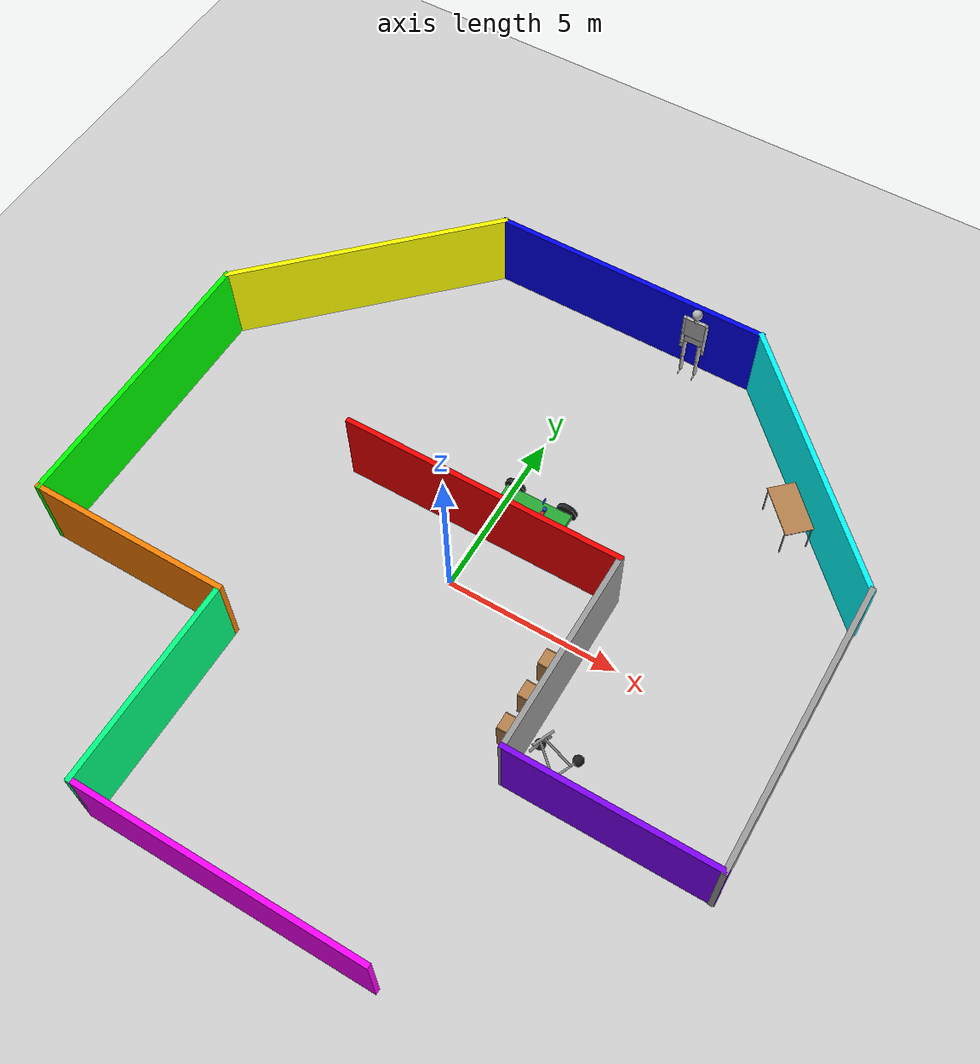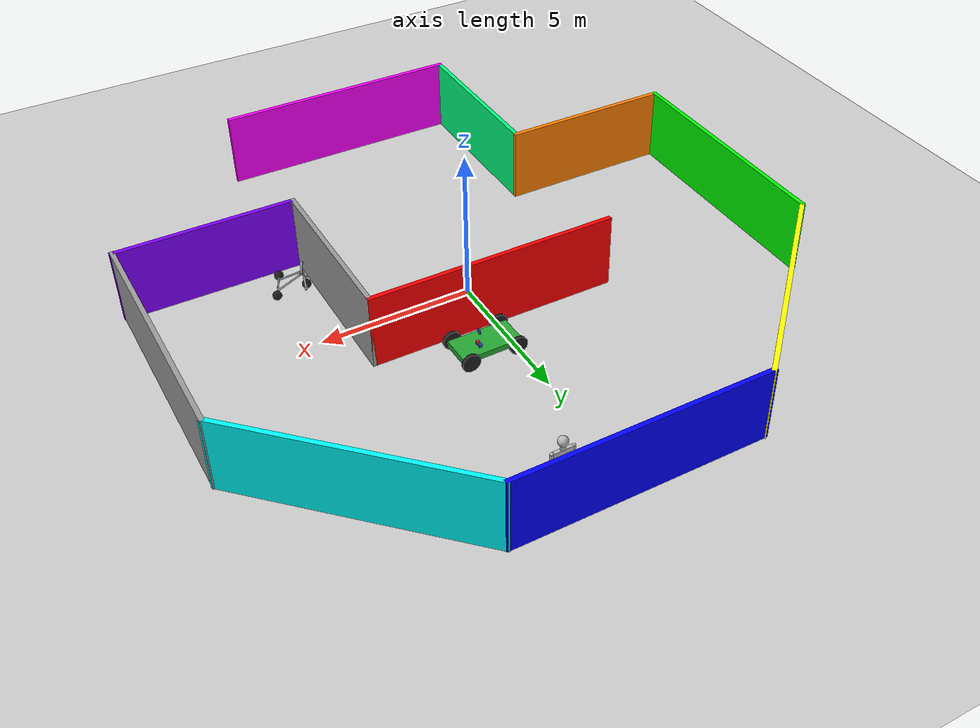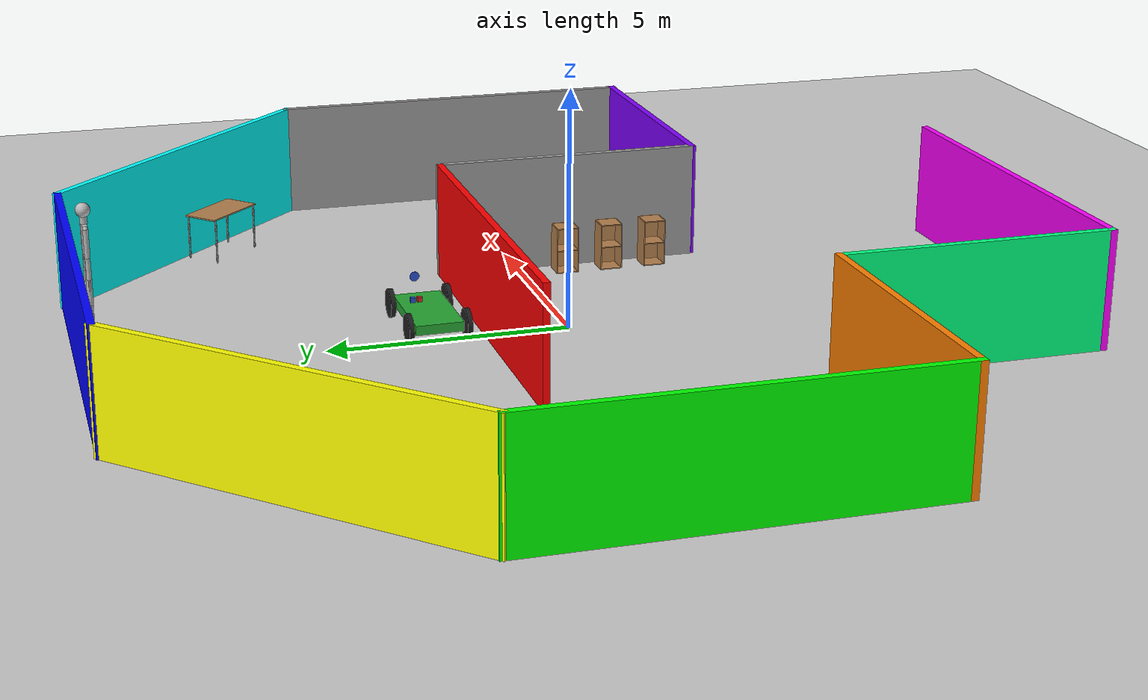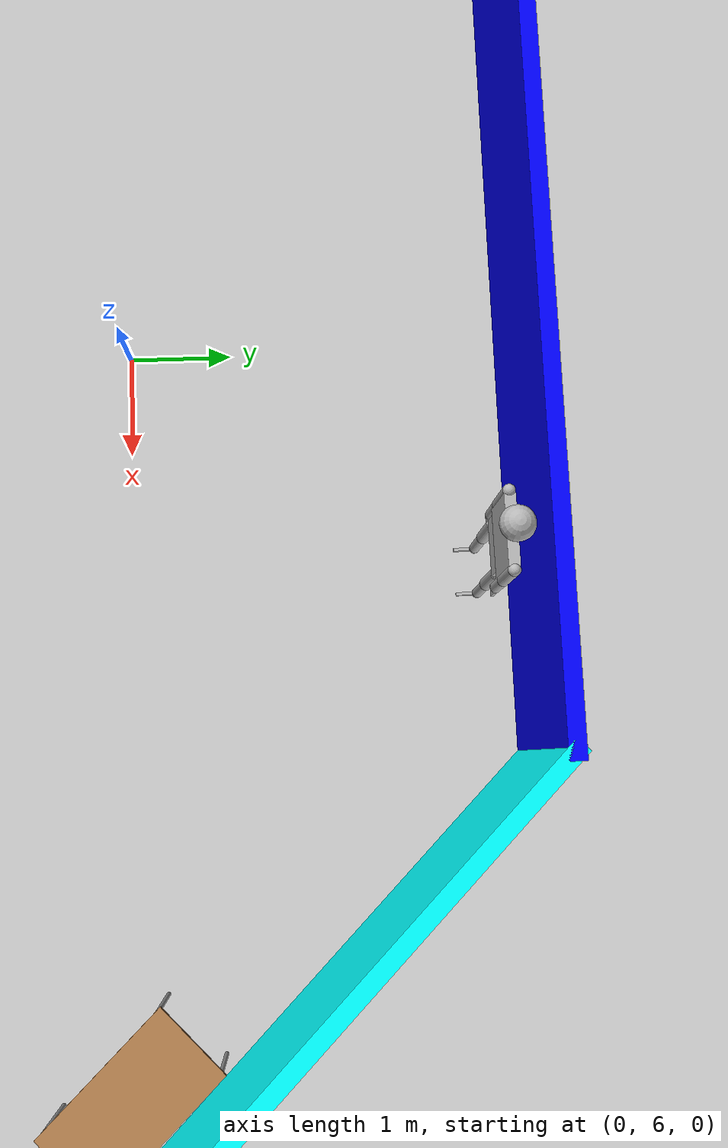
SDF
<sdf version="1.6">
 <world name="default">
  <light name="sun" type="directional">
   <pose>0 0 10 0 -0 0</pose>
   <diffuse>0.8 0.8 0.8 1</diffuse>
   <specular>0.1 0.1 0.1 1</specular>
   <attenuation>
    <range>1000</range>
    <constant>0.9</constant>
    <linear>0.01</linear>
    <quadratic>0.001</quadratic>
   </attenuation>
   <direction>-0.5 0.5 -1</direction>
  </light>
  <model name="ground_plane">
   <static>1</static>
   <link name="link">
    <collision name="collision">
     <geometry><plane><normal>0 0 1</normal><size>100 100</size></plane></geometry>
     <surface><friction><ode><mu>100</mu><mu2>50</mu2></ode></friction></surface>
    </collision>
    <visual name="visual">
     <cast_shadows>0</cast_shadows>
     <geometry><plane><normal>0 0 1</normal><size>100 100</size></plane></geometry>
     <material>
      <script><uri>file://media/materials/scripts/gazebo.material</uri><name>Gazebo/Grey</name></script>
     </material>
    </visual>
   </link>
  </model>
  <gravity>0 0 -9.8</gravity>
  <magnetic_field>6e-06 2.3e-05 -4.2e-05</magnetic_field>
  <atmosphere type="adiabatic"/>
  <physics name="default_physics" default="0" type="ode">
   <max_step_size>0.001</max_step_size>
   <real_time_factor>1</real_time_factor>
   <real_time_update_rate>1000</real_time_update_rate>
  </physics>
  <scene><ambient>0.4 0.4 0.4 1</ambient><background>0.7 0.7 0.7 1</background><shadows>1</shadows></scene>
  <spherical_coordinates>
   <surface_model>EARTH_WGS84</surface_model>
   <latitude_deg>0</latitude_deg>
   <longitude_deg>0</longitude_deg>
   <elevation>0</elevation>
   <heading_deg>0</heading_deg>
  </spherical_coordinates>
  <model name="localize_room">
   <link name="Wall_15">
    <collision name="Wall_15_Collision">
     <geometry><box><size>8.284 0.15 2.5</size></box></geometry>
     <pose>0 0 1.25 0 -0 0</pose>
    </collision>
    <visual name="Wall_15_Visual">
     <pose>0 0 1.25 0 -0 0</pose>
     <geometry><box><size>8.284 0.15 2.5</size></box></geometry>
     <material>
      <script><uri>file://media/materials/scripts/gazebo.material</uri><name>Gazebo/Grey</name></script>
      <ambient>0.0 0.0 0.0 1</ambient>
     </material>
     <meta><layer>0</layer></meta>
    </visual>
    <pose>9.775 -0.015533 0 0 -0 1.5708</pose>
   </link>
   <link name="Wall_21">
    <collision name="Wall_21_Collision">
     <geometry><box><size>8.25 0.15 2.5</size></box></geometry>
     <pose>0 0 1.25 0 -0 0</pose>
    </collision>
    <visual name="Wall_21_Visual">
     <pose>0 0 1.25 0 -0 0</pose>
     <geometry><box><size>8.25 0.15 2.5</size></box></geometry>
     <material>
      <script><uri>file://media/materials/scripts/gazebo.material</uri><name>Gazebo/Grey</name></script>
      <ambient>0.0 1.0 0.0 1</ambient>
     </material>
     <meta><layer>0</layer></meta>
    </visual>
    <pose>-9.775 0.001467 0 0 -0 1.5708</pose>
   </link>
   <link name="Wall_27">
    <collision name="Wall_27_Collision">
     <geometry><box><size>8.284 0.15 2.5</size></box></geometry>
     <pose>0 0 1.25 0 -0 0</pose>
    </collision>
    <visual name="Wall_27_Visual">
     <pose>0 0 1.25 0 -0 0</pose>
     <geometry><box><size>8.284 0.15 2.5</size></box></geometry>
     <material>
      <script><uri>file://media/materials/scripts/gazebo.material</uri><name>Gazebo/Grey</name></script>
      <ambient>0.0 0.0 1.0 1</ambient>
     </material>
     <meta><layer>0</layer></meta>
    </visual>
    <pose>0 9.75947 0 0 -0 0</pose>
   </link>
   <link name="Wall_33">
    <collision name="Wall_33_Collision">
     <geometry><box><size>8.22233 0.15 2.5</size></box></geometry>
     <pose>0 0 1.25 0 -0 0</pose>
    </collision>
    <visual name="Wall_33_Visual">
     <pose>0 0 1.25 0 -0 0</pose>
     <geometry><box><size>8.22233 0.15 2.5</size></box></geometry>
     <material>
      <script><uri>file://media/materials/scripts/gazebo.material</uri><name>Gazebo/Grey</name></script>
      <ambient>1.0 1.0 0.0 1</ambient>
     </material>
     <meta><layer>0</layer></meta>
    </visual>
    <pose>-6.921 6.90547 0 0 0 -2.35619</pose>
   </link>
   <link name="Wall_35">
    <collision name="Wall_35_Collision">
     <geometry><box><size>8.22233 0.15 2.5</size></box></geometry>
     <pose>0 0 1.25 0 -0 0</pose>
    </collision>
    <visual name="Wall_35_Visual">
     <pose>0 0 1.25 0 -0 0</pose>
     <geometry><box><size>8.22233 0.15 2.5</size></box></geometry>
     <material>
      <script><uri>file://media/materials/scripts/gazebo.material</uri><name>Gazebo/Grey</name></script>
      <ambient>0.0 1.0 1.0 1</ambient>
     </material>
     <meta><layer>0</layer></meta>
    </visual>
    <pose>6.921 6.90547 0 0 0 -0.785398</pose>
   </link>
   <link name="Wall_4">
    <collision name="Wall_4_Collision">
     <geometry><box><size>8.284 0.15 2.5</size></box></geometry>
     <pose>0 0 1.25 0 -0 0</pose>
    </collision>
    <visual name="Wall_4_Visual">
     <pose>0 0 1.25 0 -0 0</pose>
     <geometry><box><size>8.284 0.15 2.5</size></box></geometry>
     <material>
      <script><uri>file://media/materials/scripts/gazebo.material</uri><name>Gazebo/Grey</name></script>
      <ambient>1.0 0.0 1.0 1</ambient>
     </material>
     <meta><layer>0</layer></meta>
    </visual>
    <pose>0 -9.79053 0 0 -0 0</pose>
   </link>
   <link name="Wall_56">
    <collision name="Wall_56_Collision">
     <geometry><box><size>5.858 0.15 2.5</size></box></geometry>
     <pose>0 0 1.25 0 -0 0</pose>
    </collision>
    <visual name="Wall_56_Visual">
     <pose>0 0 1.25 0 -0 0</pose>
     <geometry><box><size>5.858 0.15 2.5</size></box></geometry>
     <material>
      <script><uri>file://media/materials/scripts/gazebo.material</uri><name>Gazebo/Grey</name></script>
      <ambient>1.0 0.50196 0.0 1</ambient>
     </material>
     <meta><layer>0</layer></meta>
    </visual>
    <pose>-6.921 -4.04853 0 0 -0 0</pose>
   </link>
   <link name="Wall_58">
    <collision name="Wall_58_Collision">
     <geometry><box><size>5.75 0.15 2.5</size></box></geometry>
     <pose>0 0 1.25 0 -0 0</pose>
    </collision>
    <visual name="Wall_58_Visual">
     <pose>0 0 1.25 0 -0 0</pose>
     <geometry><box><size>5.75 0.15 2.5</size></box></geometry>
     <material>
      <script><uri>file://media/materials/scripts/gazebo.material</uri><name>Gazebo/Grey</name></script>
      <ambient>0.0 1.0 0.50196 1</ambient>
     </material>
     <meta><layer>0</layer></meta>
    </visual>
    <pose>-4.067 -6.99053 0 0 -0 1.5708</pose>
   </link>
   <link name="Wall_60">
    <collision name="Wall_60_Collision">
     <geometry><box><size>5.90863 0.15 2.5</size></box></geometry>
     <pose>0 0 1.25 0 -0 0</pose>
    </collision>
    <visual name="Wall_60_Visual">
     <pose>0 0 1.25 0 -0 0</pose>
     <geometry><box><size>5.90863 0.15 2.5</size></box></geometry>
     <material>
      <script><uri>file://media/materials/scripts/gazebo.material</uri><name>Gazebo/Grey</name></script>
      <ambient>0.50196 0.0 1.0 1</ambient>
     </material>
     <meta><layer>0</layer></meta>
    </visual>
    <pose>6.91525 -4.06048 0 0 0 -0.000864</pose>
   </link>
   <link name="Wall_63">
    <collision name="Wall_63_Collision">
     <geometry><box><size>8.25 0.15 2.5</size></box></geometry>
     <pose>0 0 1.25 0 -0 0</pose>
    </collision>
    <visual name="Wall_63_Visual">
     <pose>0 0 1.25 0 -0 0</pose>
     <geometry><box><size>8.25 0.15 2.5</size></box></geometry>
     <material>
      <script><uri>file://media/materials/scripts/gazebo.material</uri><name>Gazebo/Grey</name></script>
      <ambient>1.0 0.0 0.0 1</ambient>
     </material>
     <meta><layer>0</layer></meta>
    </visual>
    <pose>-0.014065 1.69201 0 0 -0 0</pose>
   </link>
   <link name="Wall_64">
    <collision name="Wall_64_Collision">
     <geometry><box><size>5.9 0.15 2.5</size></box></geometry>
     <pose>0 0 1.25 0 -0 0</pose>
    </collision>
    <visual name="Wall_64_Visual">
     <pose>0 0 1.25 0 -0 0</pose>
     <geometry><box><size>5.9 0.15 2.5</size></box></geometry>
     <material>
      <script><uri>file://media/materials/scripts/gazebo.material</uri><name>Gazebo/Grey</name></script>
      <ambient>1.0 1.0 1.0 1</ambient>
     </material>
     <meta><layer>0</layer></meta>
    </visual>
    <pose>4.03594 -1.18299 0 0 0 -1.5708</pose>
   </link>
   <static>1</static>
  </model>
  <model name="cabinet">
   <static>1</static>
   <link name="cabinet_bottom_plate">
    <inertial>
     <pose>0 0 -1 0 -0 0</pose>
     <inertia><ixx>2.05</ixx><ixy>0</ixy><ixz>0</ixz><iyy>2.05</iyy><iyz>0</iyz><izz>2.05</izz></inertia>
     <mass>25</mass>
    </inertial>
    <collision name="cabinet_bottom_plate_geom">
     <pose>0 0 0.01 0 -0 0</pose>
     <geometry><box><size>0.45 0.45 0.02</size></box></geometry>
    </collision>
    <visual name="cabinet_bottom_plate_geom_visual">
     <pose>0 0 0.01 0 -0 0</pose>
     <geometry><box><size>0.45 0.45 0.02</size></box></geometry>
     <material>
      <script><uri>file://media/materials/scripts/gazebo.material</uri><name>Gazebo/Wood</name></script>
     </material>
    </visual>
    <collision name="cabinet_bottom_plate_geom_cabinet_back_plate">
     <pose>0.235 0 0.51 0 -0 0</pose>
     <geometry><box><size>0.02 0.45 1.02</size></box></geometry>
    </collision>
    <visual name="cabinet_bottom_plate_geom_cabinet_back_plate_visual">
     <pose>0.235 0 0.51 0 -0 0</pose>
     <geometry><box><size>0.02 0.45 1.02</size></box></geometry>
     <material>
      <script><uri>file://media/materials/scripts/gazebo.material</uri><name>Gazebo/Wood</name></script>
     </material>
    </visual>
    <collision name="cabinet_bottom_plate_geom_cabinet_left_plate">
     <pose>0 0.235 0.51 0 -0 0</pose>
     <geometry><box><size>0.45 0.02 1.02</size></box></geometry>
    </collision>
    <visual name="cabinet_bottom_plate_geom_cabinet_left_plate_visual">
     <pose>0 0.235 0.51 0 -0 0</pose>
     <geometry><box><size>0.45 0.02 1.02</size></box></geometry>
     <material>
      <script><uri>file://media/materials/scripts/gazebo.material</uri><name>Gazebo/Wood</name></script>
     </material>
    </visual>
    <collision name="cabinet_bottom_plate_geom_cabinet_middle_plate">
     <pose>0 0 0.51 0 -0 0</pose>
     <geometry><box><size>0.45 0.45 0.02</size></box></geometry>
    </collision>
    <visual name="cabinet_bottom_plate_geom_cabinet_middle_plate_visual">
     <pose>0 0 0.51 0 -0 0</pose>
     <geometry><box><size>0.45 0.45 0.02</size></box></geometry>
     <material>
      <script><uri>file://media/materials/scripts/gazebo.material</uri><name>Gazebo/Wood</name></script>
     </material>
    </visual>
    <collision name="cabinet_bottom_plate_geom_cabinet_right_plate">
     <pose>0 -0.235 0.51 0 -0 0</pose>
     <geometry><box><size>0.45 0.02 1.02</size></box></geometry>
    </collision>
    <visual name="cabinet_bottom_plate_geom_cabinet_right_plate_visual">
     <pose>0 -0.235 0.51 0 -0 0</pose>
     <geometry><box><size>0.45 0.02 1.02</size></box></geometry>
     <material>
      <script><uri>file://media/materials/scripts/gazebo.material</uri><name>Gazebo/Wood</name></script>
     </material>
    </visual>
    <collision name="cabinet_bottom_plate_geom_cabinet_top_plate">
     <pose>0 0 1.01 0 -0 0</pose>
     <geometry><box><size>0.45 0.45 0.02</size></box></geometry>
    </collision>
    <visual name="cabinet_bottom_plate_geom_cabinet_top_plate_visual">
     <pose>0 0 1.01 0 -0 0</pose>
     <geometry><box><size>0.45 0.45 0.02</size></box></geometry>
     <material>
      <script><uri>file://media/materials/scripts/gazebo.material</uri><name>Gazebo/Wood</name></script>
     </material>
    </visual>
   </link>
   <pose>3.6 -3 0 0 -0 0</pose>
  </model>
  <model name="cabinet_0">
   <static>1</static>
   <link name="cabinet_bottom_plate">
    <inertial>
     <pose>0 0 -1 0 -0 0</pose>
     <inertia><ixx>2.05</ixx><ixy>0</ixy><ixz>0</ixz><iyy>2.05</iyy><iyz>0</iyz><izz>2.05</izz></inertia>
     <mass>25</mass>
    </inertial>
    <collision name="cabinet_bottom_plate_geom">
     <pose>0 0 0.01 0 -0 0</pose>
     <geometry><box><size>0.45 0.45 0.02</size></box></geometry>
    </collision>
    <visual name="cabinet_bottom_plate_geom_visual">
     <pose>0 0 0.01 0 -0 0</pose>
     <geometry><box><size>0.45 0.45 0.02</size></box></geometry>
     <material>
      <script><uri>file://media/materials/scripts/gazebo.material</uri><name>Gazebo/Wood</name></script>
     </material>
    </visual>
    <collision name="cabinet_bottom_plate_geom_cabinet_back_plate">
     <pose>0.235 0 0.51 0 -0 0</pose>
     <geometry><box><size>0.02 0.45 1.02</size></box></geometry>
    </collision>
    <visual name="cabinet_bottom_plate_geom_cabinet_back_plate_visual">
     <pose>0.235 0 0.51 0 -0 0</pose>
     <geometry><box><size>0.02 0.45 1.02</size></box></geometry>
     <material>
      <script><uri>file://media/materials/scripts/gazebo.material</uri><name>Gazebo/Wood</name></script>
     </material>
    </visual>
    <collision name="cabinet_bottom_plate_geom_cabinet_left_plate">
     <pose>0 0.235 0.51 0 -0 0</pose>
     <geometry><box><size>0.45 0.02 1.02</size></box></geometry>
    </collision>
    <visual name="cabinet_bottom_plate_geom_cabinet_left_plate_visual">
     <pose>0 0.235 0.51 0 -0 0</pose>
     <geometry><box><size>0.45 0.02 1.02</size></box></geometry>
     <material>
      <script><uri>file://media/materials/scripts/gazebo.material</uri><name>Gazebo/Wood</name></script>
     </material>
    </visual>
    <collision name="cabinet_bottom_plate_geom_cabinet_middle_plate">
     <pose>0 0 0.51 0 -0 0</pose>
     <geometry><box><size>0.45 0.45 0.02</size></box></geometry>
    </collision>
    <visual name="cabinet_bottom_plate_geom_cabinet_middle_plate_visual">
     <pose>0 0 0.51 0 -0 0</pose>
     <geometry><box><size>0.45 0.45 0.02</size></box></geometry>
     <material>
      <script><uri>file://media/materials/scripts/gazebo.material</uri><name>Gazebo/Wood</name></script>
     </material>
    </visual>
    <collision name="cabinet_bottom_plate_geom_cabinet_right_plate">
     <pose>0 -0.235 0.51 0 -0 0</pose>
     <geometry><box><size>0.45 0.02 1.02</size></box></geometry>
    </collision>
    <visual name="cabinet_bottom_plate_geom_cabinet_right_plate_visual">
     <pose>0 -0.235 0.51 0 -0 0</pose>
     <geometry><box><size>0.45 0.02 1.02</size></box></geometry>
     <material>
      <script><uri>file://media/materials/scripts/gazebo.material</uri><name>Gazebo/Wood</name></script>
     </material>
    </visual>
    <collision name="cabinet_bottom_plate_geom_cabinet_top_plate">
     <pose>0 0 1.01 0 -0 0</pose>
     <geometry><box><size>0.45 0.45 0.02</size></box></geometry>
    </collision>
    <visual name="cabinet_bottom_plate_geom_cabinet_top_plate_visual">
     <pose>0 0 1.01 0 -0 0</pose>
     <geometry><box><size>0.45 0.45 0.02</size></box></geometry>
     <material>
      <script><uri>file://media/materials/scripts/gazebo.material</uri><name>Gazebo/Wood</name></script>
     </material>
    </visual>
   </link>
   <pose>3.6 -2 0 0 -0 0</pose>
  </model>
  <model name="cabinet_1">
   <static>1</static>
   <link name="cabinet_bottom_plate">
    <inertial>
     <pose>0 0 -1 0 -0 0</pose>
     <inertia><ixx>2.05</ixx><ixy>0</ixy><ixz>0</ixz><iyy>2.05</iyy><iyz>0</iyz><izz>2.05</izz></inertia>
     <mass>25</mass>
    </inertial>
    <collision name="cabinet_bottom_plate_geom">
     <pose>0 0 0.01 0 -0 0</pose>
     <geometry><box><size>0.45 0.45 0.02</size></box></geometry>
    </collision>
    <visual name="cabinet_bottom_plate_geom_visual">
     <pose>0 0 0.01 0 -0 0</pose>
     <geometry><box><size>0.45 0.45 0.02</size></box></geometry>
     <material>
      <script><uri>file://media/materials/scripts/gazebo.material</uri><name>Gazebo/Wood</name></script>
     </material>
    </visual>
    <collision name="cabinet_bottom_plate_geom_cabinet_back_plate">
     <pose>0.235 0 0.51 0 -0 0</pose>
     <geometry><box><size>0.02 0.45 1.02</size></box></geometry>
    </collision>
    <visual name="cabinet_bottom_plate_geom_cabinet_back_plate_visual">
     <pose>0.235 0 0.51 0 -0 0</pose>
     <geometry><box><size>0.02 0.45 1.02</size></box></geometry>
     <material>
      <script><uri>file://media/materials/scripts/gazebo.material</uri><name>Gazebo/Wood</name></script>
     </material>
    </visual>
    <collision name="cabinet_bottom_plate_geom_cabinet_left_plate">
     <pose>0 0.235 0.51 0 -0 0</pose>
     <geometry><box><size>0.45 0.02 1.02</size></box></geometry>
    </collision>
    <visual name="cabinet_bottom_plate_geom_cabinet_left_plate_visual">
     <pose>0 0.235 0.51 0 -0 0</pose>
     <geometry><box><size>0.45 0.02 1.02</size></box></geometry>
     <material>
      <script><uri>file://media/materials/scripts/gazebo.material</uri><name>Gazebo/Wood</name></script>
     </material>
    </visual>
    <collision name="cabinet_bottom_plate_geom_cabinet_middle_plate">
     <pose>0 0 0.51 0 -0 0</pose>
     <geometry><box><size>0.45 0.45 0.02</size></box></geometry>
    </collision>
    <visual name="cabinet_bottom_plate_geom_cabinet_middle_plate_visual">
     <pose>0 0 0.51 0 -0 0</pose>
     <geometry><box><size>0.45 0.45 0.02</size></box></geometry>
     <material>
      <script><uri>file://media/materials/scripts/gazebo.material</uri><name>Gazebo/Wood</name></script>
     </material>
    </visual>
    <collision name="cabinet_bottom_plate_geom_cabinet_right_plate">
     <pose>0 -0.235 0.51 0 -0 0</pose>
     <geometry><box><size>0.45 0.02 1.02</size></box></geometry>
    </collision>
    <visual name="cabinet_bottom_plate_geom_cabinet_right_plate_visual">
     <pose>0 -0.235 0.51 0 -0 0</pose>
     <geometry><box><size>0.45 0.02 1.02</size></box></geometry>
     <material>
      <script><uri>file://media/materials/scripts/gazebo.material</uri><name>Gazebo/Wood</name></script>
     </material>
    </visual>
    <collision name="cabinet_bottom_plate_geom_cabinet_top_plate">
     <pose>0 0 1.01 0 -0 0</pose>
     <geometry><box><size>0.45 0.45 0.02</size></box></geometry>
    </collision>
    <visual name="cabinet_bottom_plate_geom_cabinet_top_plate_visual">
     <pose>0 0 1.01 0 -0 0</pose>
     <geometry><box><size>0.45 0.45 0.02</size></box></geometry>
     <material>
      <script><uri>file://media/materials/scripts/gazebo.material</uri><name>Gazebo/Wood</name></script>
     </material>
    </visual>
   </link>
   <pose>3.6 -1 0 0 -0 0</pose>
  </model>
  <model name="table">
   <static>1</static>
   <link name="link">
    <collision name="surface">
     <pose>0 0 1 0 -0 0</pose>
     <geometry><box><size>1.5 0.8 0.03</size></box></geometry>
     <surface><friction><ode><mu>0.6</mu><mu2>0.6</mu2></ode></friction></surface>
    </collision>
    <visual name="visual1">
     <pose>0 0 1 0 -0 0</pose>
     <geometry><box><size>1.5 0.8 0.03</size></box></geometry>
     <material>
      <script><uri>file://media/materials/scripts/gazebo.material</uri><name>Gazebo/Wood</name></script>
     </material>
    </visual>
    <collision name="front_left_leg">
     <pose>0.68 0.38 0.5 0 -0 0</pose>
     <geometry><cylinder><radius>0.02</radius><length>1</length></cylinder></geometry>
    </collision>
    <visual name="front_left_leg">
     <pose>0.68 0.38 0.5 0 -0 0</pose>
     <geometry><cylinder><radius>0.02</radius><length>1</length></cylinder></geometry>
     <material>
      <script><uri>file://media/materials/scripts/gazebo.material</uri><name>Gazebo/Grey</name></script>
     </material>
    </visual>
    <collision name="front_right_leg">
     <pose>0.68 -0.38 0.5 0 -0 0</pose>
     <geometry><cylinder><radius>0.02</radius><length>1</length></cylinder></geometry>
    </collision>
    <visual name="front_right_leg">
     <pose>0.68 -0.38 0.5 0 -0 0</pose>
     <geometry><cylinder><radius>0.02</radius><length>1</length></cylinder></geometry>
     <material>
      <script><uri>file://media/materials/scripts/gazebo.material</uri><name>Gazebo/Grey</name></script>
     </material>
    </visual>
    <collision name="back_right_leg">
     <pose>-0.68 -0.38 0.5 0 -0 0</pose>
     <geometry><cylinder><radius>0.02</radius><length>1</length></cylinder></geometry>
    </collision>
    <visual name="back_right_leg">
     <pose>-0.68 -0.38 0.5 0 -0 0</pose>
     <geometry><cylinder><radius>0.02</radius><length>1</length></cylinder></geometry>
     <material>
      <script><uri>file://media/materials/scripts/gazebo.material</uri><name>Gazebo/Grey</name></script>
     </material>
    </visual>
    <collision name="back_left_leg">
     <pose>-0.68 0.38 0.5 0 -0 0</pose>
     <geometry><cylinder><radius>0.02</radius><length>1</length></cylinder></geometry>
    </collision>
    <visual name="back_left_leg">
     <pose>-0.68 0.38 0.5 0 -0 0</pose>
     <geometry><cylinder><radius>0.02</radius><length>1</length></cylinder></geometry>
     <material>
      <script><uri>file://media/materials/scripts/gazebo.material</uri><name>Gazebo/Grey</name></script>
     </material>
    </visual>
   </link>
   <pose>6.91018 6.07308 0 0 0 -0.801836</pose>
  </model>
  <model name="trisphere_cycle">
   <link name="frame">
    <pose>-0.408559 0 0.385023 0 -0.522021 0</pose>
    <inertial>
     <mass>10</mass>
     <inertia><ixx>0.228</ixx><iyy>0.743521</iyy><izz>0.965521</izz><ixy>0</ixy><ixz>0</ixz><iyz>0</iyz></inertia>
    </inertial>
    <collision name="axle_collision">
     <pose>-0.471335 0 0 1.5708 -0 0</pose>
     <geometry><cylinder><length>1.03923</length><radius>0.03</radius></cylinder></geometry>
    </collision>
    <visual name="axle_visual">
     <pose>-0.471335 0 0 1.5708 -0 0</pose>
     <geometry><cylinder><length>1.03923</length><radius>0.03</radius></cylinder></geometry>
     <material>
      <script><uri>file://media/materials/scripts/gazebo.material</uri><name>Gazebo/Grey</name></script>
     </material>
    </visual>
    <collision name="frame_left_collision">
     <pose>0 0.171552 0 2.986 1.57079 2.76675</pose>
     <geometry><cylinder><length>1.00317</length><radius>0.03</radius></cylinder></geometry>
    </collision>
    <visual name="frame_left_visual">
     <pose>0 0.171552 0 2.986 1.57079 2.76675</pose>
     <geometry><cylinder><length>1.00317</length><radius>0.03</radius></cylinder></geometry>
     <material>
      <script><uri>file://media/materials/scripts/gazebo.material</uri><name>Gazebo/Grey</name></script>
     </material>
    </visual>
    <collision name="frame_right_collision">
     <pose>0 -0.171552 0 -2.986 1.57079 -2.76675</pose>
     <geometry><cylinder><length>1.00317</length><radius>0.03</radius></cylinder></geometry>
    </collision>
    <visual name="frame_right_visual">
     <pose>0 -0.171552 0 -2.986 1.57079 -2.76675</pose>
     <geometry><cylinder><length>1.00317</length><radius>0.03</radius></cylinder></geometry>
     <material>
      <script><uri>file://media/materials/scripts/gazebo.material</uri><name>Gazebo/Grey</name></script>
     </material>
    </visual>
   </link>
   <link name="fork">
    <pose>0.041441 0 0.385023 0 -0.174533 0</pose>
    <inertial>
     <mass>3</mass>
     <inertia>
      <ixx>0.158203</ixx>
      <iyy>0.0583594</iyy>
      <izz>0.102656</izz>
      <ixy>0</ixy>
      <ixz>0</ixz>
      <iyz>0</iyz>
     </inertia>
    </inertial>
    <collision name="handlebars_collision">
     <pose>0 0 0.397748 1.5708 -0 0</pose>
     <geometry><cylinder><length>0.636396</length><radius>0.0375</radius></cylinder></geometry>
    </collision>
    <visual name="handlebars_visual">
     <pose>0 0 0.397748 1.5708 -0 0</pose>
     <geometry><cylinder><length>0.636396</length><radius>0.0375</radius></cylinder></geometry>
     <material>
      <script><uri>file://media/materials/scripts/gazebo.material</uri><name>Gazebo/Grey</name></script>
     </material>
    </visual>
    <collision name="headtube_collision">
     <pose>0 0 0.238649 0 -0 0</pose>
     <geometry><cylinder><length>0.318198</length><radius>0.0375</radius></cylinder></geometry>
    </collision>
    <visual name="headtube_visual">
     <pose>0 0 0.238649 0 -0 0</pose>
     <geometry><cylinder><length>0.318198</length><radius>0.0375</radius></cylinder></geometry>
     <material>
      <script><uri>file://media/materials/scripts/gazebo.material</uri><name>Gazebo/Grey</name></script>
     </material>
    </visual>
    <collision name="spindle_collision">
     <pose>0 0 -0.238649 1.5708 -0 0</pose>
     <geometry><cylinder><length>0.636396</length><radius>0.015</radius></cylinder></geometry>
    </collision>
    <visual name="spindle_visual">
     <pose>0 0 -0.238649 1.5708 -0 0</pose>
     <geometry><cylinder><length>0.636396</length><radius>0.015</radius></cylinder></geometry>
     <material>
      <script><uri>file://media/materials/scripts/gazebo.material</uri><name>Gazebo/Grey</name></script>
     </material>
    </visual>
    <collision name="fork_left_collision">
     <pose>0 0.159099 -0.07955 0.785398 -0 0</pose>
     <geometry><cylinder><length>0.45</length><radius>0.0375</radius></cylinder></geometry>
    </collision>
    <visual name="fork_left_visual">
     <pose>0 0.159099 -0.07955 0.785398 -0 0</pose>
     <geometry><cylinder><length>0.45</length><radius>0.0375</radius></cylinder></geometry>
     <material>
      <script><uri>file://media/materials/scripts/gazebo.material</uri><name>Gazebo/Grey</name></script>
     </material>
    </visual>
    <collision name="fork_right_collision">
     <pose>0 -0.159099 -0.07955 -0.785398 0 0</pose>
     <geometry><cylinder><length>0.45</length><radius>0.0375</radius></cylinder></geometry>
    </collision>
    <visual name="fork_right_visual">
     <pose>0 -0.159099 -0.07955 -0.785398 0 0</pose>
     <geometry><cylinder><length>0.45</length><radius>0.0375</radius></cylinder></geometry>
     <material>
      <script><uri>file://media/materials/scripts/gazebo.material</uri><name>Gazebo/Grey</name></script>
     </material>
    </visual>
   </link>
   <link name="wheel_front">
    <pose>0.082882 0 0.15 0 -0 0</pose>
    <inertial>
     <mass>0.5</mass>
     <inertia><ixx>0.0045</ixx><iyy>0.0045</iyy><izz>0.0045</izz><ixy>0</ixy><ixz>0</ixz><iyz>0</iyz></inertia>
    </inertial>
    <collision name="collision">
     <geometry><sphere><radius>0.15</radius></sphere></geometry>
     <surface><contact><ode><kp>1e+08</kp><kd>1</kd><min_depth>0.0005</min_depth></ode></contact></surface>
    </collision>
    <visual name="visual">
     <geometry><sphere><radius>0.15</radius></sphere></geometry>
     <material>
      <script><uri>file://media/materials/scripts/gazebo.material</uri><name>Gazebo/Black</name></script>
     </material>
    </visual>
   </link>
   <joint name="wheel_front_steer" type="revolute">
    <parent>frame</parent>
    <child>fork</child>
    <axis>
     <xyz>0 0 1</xyz>
     <limit><lower>-0.959931</lower><upper>0.959931</upper></limit>
     <use_parent_model_frame>0</use_parent_model_frame>
     <dynamics><spring_reference>0</spring_reference><spring_stiffness>0</spring_stiffness></dynamics>
    </axis>
   </joint>
   <joint name="wheel_front_spin" type="revolute">
    <parent>fork</parent>
    <child>wheel_front</child>
    <axis>
     <xyz>0 1 0</xyz>
     <use_parent_model_frame>0</use_parent_model_frame>
     <limit><lower>-1e+16</lower><upper>1e+16</upper></limit>
     <dynamics><spring_reference>0</spring_reference><spring_stiffness>0</spring_stiffness></dynamics>
    </axis>
   </joint>
   <link name="wheel_rear_left">
    <pose>-0.817118 0.519615 0.15 0 -0 0</pose>
    <inertial>
     <mass>0.5</mass>
     <inertia><ixx>0.0045</ixx><iyy>0.0045</iyy><izz>0.0045</izz><ixy>0</ixy><ixz>0</ixz><iyz>0</iyz></inertia>
    </inertial>
    <collision name="collision">
     <geometry><sphere><radius>0.15</radius></sphere></geometry>
     <surface><contact><ode><kp>1e+08</kp><kd>1</kd><min_depth>0.0005</min_depth></ode></contact></surface>
    </collision>
    <visual name="visual">
     <geometry><sphere><radius>0.15</radius></sphere></geometry>
     <material>
      <script><uri>file://media/materials/scripts/gazebo.material</uri><name>Gazebo/Black</name></script>
     </material>
    </visual>
   </link>
   <joint name="wheel_rear_left_spin" type="revolute">
    <parent>frame</parent>
    <child>wheel_rear_left</child>
    <axis>
     <xyz>0 1 0</xyz>
     <use_parent_model_frame>0</use_parent_model_frame>
     <limit><lower>-1e+16</lower><upper>1e+16</upper></limit>
     <dynamics><spring_reference>0</spring_reference><spring_stiffness>0</spring_stiffness></dynamics>
    </axis>
   </joint>
   <link name="wheel_rear_right">
    <pose>-0.817118 -0.519615 0.15 0 -0 0</pose>
    <inertial>
     <mass>0.5</mass>
     <inertia><ixx>0.0045</ixx><iyy>0.0045</iyy><izz>0.0045</izz><ixy>0</ixy><ixz>0</ixz><iyz>0</iyz></inertia>
    </inertial>
    <collision name="collision">
     <geometry><sphere><radius>0.15</radius></sphere></geometry>
     <surface><contact><ode><kp>1e+08</kp><kd>1</kd><min_depth>0.0005</min_depth></ode></contact></surface>
    </collision>
    <visual name="visual">
     <geometry><sphere><radius>0.15</radius></sphere></geometry>
     <material>
      <script><uri>file://media/materials/scripts/gazebo.material</uri><name>Gazebo/Black</name></script>
     </material>
    </visual>
   </link>
   <joint name="wheel_rear_right_spin" type="revolute">
    <parent>frame</parent>
    <child>wheel_rear_right</child>
    <axis>
     <xyz>0 1 0</xyz>
     <use_parent_model_frame>0</use_parent_model_frame>
     <limit><lower>-1e+16</lower><upper>1e+16</upper></limit>
     <dynamics><spring_reference>0</spring_reference><spring_stiffness>0</spring_stiffness></dynamics>
    </axis>
   </joint>
   <pose>4.4301 -2.79774 -0.000501 -0 1e-06 2.72369</pose>
  </model>
  <model name="car">
   <link name="chassis">
    <pose>0 0 0.3 0 -0 0</pose>
    <collision name="collision"><geometry><box><size>2 1 0.2</size></box></geometry></collision>
    <visual name="visual">
     <geometry><box><size>2 1 0.2</size></box></geometry>
     <material>
      <script><uri>file://media/materials/scripts/gazebo.material</uri><name>Gazebo/Green</name></script>
     </material>
    </visual>
    <inertial>
     <inertia><ixx>1</ixx><ixy>0</ixy><ixz>0</ixz><iyy>1</iyy><iyz>0</iyz><izz>1</izz></inertia>
     <mass>1</mass>
    </inertial>
   </link>
   <link name="front_left_wheel">
    <pose>0.8 0.6 0.3 -0 1.5707 1.5707</pose>
    <collision name="collision">
     <geometry><cylinder><radius>0.3</radius><length>0.1</length></cylinder></geometry>
    </collision>
    <visual name="visual">
     <geometry><cylinder><radius>0.3</radius><length>0.1</length></cylinder></geometry>
     <material>
      <script><uri>file://media/materials/scripts/gazebo.material</uri><name>Gazebo/Black</name></script>
     </material>
    </visual>
    <inertial>
     <inertia><ixx>1</ixx><ixy>0</ixy><ixz>0</ixz><iyy>1</iyy><iyz>0</iyz><izz>1</izz></inertia>
     <mass>1</mass>
    </inertial>
   </link>
   <link name="front_right_wheel">
    <pose>0.8 -0.6 0.3 -0 1.5707 1.5707</pose>
    <collision name="collision">
     <geometry><cylinder><radius>0.3</radius><length>0.1</length></cylinder></geometry>
    </collision>
    <visual name="visual">
     <geometry><cylinder><radius>0.3</radius><length>0.1</length></cylinder></geometry>
     <material>
      <script><uri>file://media/materials/scripts/gazebo.material</uri><name>Gazebo/Black</name></script>
     </material>
    </visual>
    <inertial>
     <inertia><ixx>1</ixx><ixy>0</ixy><ixz>0</ixz><iyy>1</iyy><iyz>0</iyz><izz>1</izz></inertia>
     <mass>1</mass>
    </inertial>
   </link>
   <link name="back_right_wheel">
    <pose>-0.8 -0.6 0.3 -0 1.5707 1.5707</pose>
    <collision name="collision">
     <geometry><cylinder><radius>0.3</radius><length>0.1</length></cylinder></geometry>
    </collision>
    <visual name="visual">
     <geometry><cylinder><radius>0.3</radius><length>0.1</length></cylinder></geometry>
     <material>
      <script><uri>file://media/materials/scripts/gazebo.material</uri><name>Gazebo/Black</name></script>
     </material>
    </visual>
    <inertial>
     <inertia><ixx>1</ixx><ixy>0</ixy><ixz>0</ixz><iyy>1</iyy><iyz>0</iyz><izz>1</izz></inertia>
     <mass>1</mass>
    </inertial>
   </link>
   <link name="back_left_wheel">
    <pose>-0.8 0.6 0.3 -0 1.5707 1.5707</pose>
    <collision name="collision">
     <geometry><cylinder><radius>0.3</radius><length>0.1</length></cylinder></geometry>
    </collision>
    <visual name="visual">
     <geometry><cylinder><radius>0.3</radius><length>0.1</length></cylinder></geometry>
     <material>
      <script><uri>file://media/materials/scripts/gazebo.material</uri><name>Gazebo/Black</name></script>
     </material>
    </visual>
    <inertial>
     <inertia><ixx>1</ixx><ixy>0</ixy><ixz>0</ixz><iyy>1</iyy><iyz>0</iyz><izz>1</izz></inertia>
     <mass>1</mass>
    </inertial>
   </link>
   <link name="gas_pedal">
    <pose>0.3 0.1 0.5 0 -0 0</pose>
    <collision name="collision"><geometry><box><size>0.1 0.1 0.1</size></box></geometry></collision>
    <visual name="visual">
     <geometry><box><size>0.1 0.1 0.1</size></box></geometry>
     <material>
      <script><uri>file://media/materials/scripts/gazebo.material</uri><name>Gazebo/Red</name></script>
     </material>
    </visual>
    <inertial>
     <inertia><ixx>1</ixx><ixy>0</ixy><ixz>0</ixz><iyy>1</iyy><iyz>0</iyz><izz>1</izz></inertia>
     <mass>1</mass>
    </inertial>
   </link>
   <link name="brake_pedal">
    <pose>0.3 0.25 0.5 0 -0 0</pose>
    <collision name="collision"><geometry><box><size>0.1 0.1 0.1</size></box></geometry></collision>
    <visual name="visual">
     <geometry><box><size>0.1 0.1 0.1</size></box></geometry>
     <material>
      <script><uri>file://media/materials/scripts/gazebo.material</uri><name>Gazebo/Blue</name></script>
     </material>
    </visual>
    <inertial>
     <inertia><ixx>1</ixx><ixy>0</ixy><ixz>0</ixz><iyy>1</iyy><iyz>0</iyz><izz>1</izz></inertia>
     <mass>1</mass>
    </inertial>
   </link>
   <link name="steering_wheel">
    <pose>0.3 0.2 1 0 1.5707 0</pose>
    <collision name="collision">
     <geometry><cylinder><radius>0.1</radius><length>0.01</length></cylinder></geometry>
    </collision>
    <visual name="visual">
     <geometry><cylinder><radius>0.1</radius><length>0.01</length></cylinder></geometry>
     <material>
      <script><uri>file://media/materials/scripts/gazebo.material</uri><name>Gazebo/Blue</name></script>
     </material>
    </visual>
    <inertial>
     <inertia><ixx>1</ixx><ixy>0</ixy><ixz>0</ixz><iyy>1</iyy><iyz>0</iyz><izz>1</izz></inertia>
     <mass>1</mass>
    </inertial>
   </link>
   <joint name="gas_joint" type="prismatic">
    <parent>chassis</parent>
    <child>gas_pedal</child>
    <axis>
     <xyz>1 0 0</xyz>
     <limit><lower>0</lower><upper>0.2</upper></limit>
     <use_parent_model_frame>1</use_parent_model_frame>
     <dynamics><spring_reference>0</spring_reference><spring_stiffness>0</spring_stiffness></dynamics>
    </axis>
   </joint>
   <joint name="brake_joint" type="prismatic">
    <parent>chassis</parent>
    <child>brake_pedal</child>
    <axis>
     <xyz>1 0 0</xyz>
     <limit><lower>0</lower><upper>0.2</upper></limit>
     <use_parent_model_frame>1</use_parent_model_frame>
     <dynamics><spring_reference>0</spring_reference><spring_stiffness>0</spring_stiffness></dynamics>
    </axis>
   </joint>
   <joint name="steering_joint" type="revolute">
    <parent>chassis</parent>
    <child>steering_wheel</child>
    <axis>
     <xyz>1 0 0</xyz>
     <limit><lower>-7.853</lower><upper>7.853</upper></limit>
     <use_parent_model_frame>1</use_parent_model_frame>
     <dynamics><spring_reference>0</spring_reference><spring_stiffness>0</spring_stiffness></dynamics>
    </axis>
   </joint>
   <joint name="front_left_joint" type="revolute2">
    <parent>chassis</parent>
    <child>front_left_wheel</child>
    <axis>
     <xyz>0 0 1</xyz>
     <limit><lower>0.00194911</lower><upper>0.00194911</upper></limit>
     <use_parent_model_frame>1</use_parent_model_frame>
     <dynamics><spring_reference>0</spring_reference><spring_stiffness>0</spring_stiffness></dynamics>
    </axis>
    <axis2>
     <xyz>0 1 0</xyz>
     <use_parent_model_frame>1</use_parent_model_frame>
     <dynamics><spring_reference>0</spring_reference><spring_stiffness>0</spring_stiffness></dynamics>
    </axis2>
    <physics><ode><limit><cfm>0</cfm><erp>0.9</erp></limit></ode></physics>
   </joint>
   <joint name="front_right_joint" type="revolute2">
    <parent>chassis</parent>
    <child>front_right_wheel</child>
    <axis>
     <xyz>0 0 1</xyz>
     <limit><lower>0.00194911</lower><upper>0.00194911</upper></limit>
     <use_parent_model_frame>1</use_parent_model_frame>
     <dynamics><spring_reference>0</spring_reference><spring_stiffness>0</spring_stiffness></dynamics>
    </axis>
    <axis2>
     <xyz>0 1 0</xyz>
     <use_parent_model_frame>1</use_parent_model_frame>
     <dynamics><spring_reference>0</spring_reference><spring_stiffness>0</spring_stiffness></dynamics>
    </axis2>
    <physics><ode><limit><cfm>0</cfm><erp>0.9</erp></limit></ode></physics>
   </joint>
   <joint name="back_right_joint" type="revolute2">
    <parent>chassis</parent>
    <child>back_right_wheel</child>
    <axis>
     <xyz>0 0 1</xyz>
     <limit><lower>0</lower><upper>0</upper></limit>
     <use_parent_model_frame>1</use_parent_model_frame>
     <dynamics><spring_reference>0</spring_reference><spring_stiffness>0</spring_stiffness></dynamics>
    </axis>
    <axis2>
     <xyz>0 1 0</xyz>
     <use_parent_model_frame>1</use_parent_model_frame>
     <dynamics><spring_reference>0</spring_reference><spring_stiffness>0</spring_stiffness></dynamics>
    </axis2>
    <physics><ode><limit><cfm>0</cfm><erp>0.9</erp></limit></ode></physics>
   </joint>
   <joint name="back_left_joint" type="revolute2">
    <parent>chassis</parent>
    <child>back_left_wheel</child>
    <axis>
     <xyz>0 0 1</xyz>
     <limit><lower>0</lower><upper>0</upper></limit>
     <use_parent_model_frame>1</use_parent_model_frame>
     <dynamics><spring_reference>0</spring_reference><spring_stiffness>0</spring_stiffness></dynamics>
    </axis>
    <axis2>
     <xyz>0 1 0</xyz>
     <use_parent_model_frame>1</use_parent_model_frame>
     <dynamics><spring_reference>0</spring_reference><spring_stiffness>0</spring_stiffness></dynamics>
    </axis2>
    <physics><ode><limit><cfm>0</cfm><erp>0.9</erp></limit></ode></physics>
   </joint>
   <plugin name="vehicle" filename="libVehiclePlugin.so">
    <front_left>front_left_joint</front_left>
    <front_right>front_right_joint</front_right>
    <back_left>back_left_joint</back_left>
    <back_right>back_right_joint</back_right>
    <gas>gas_joint</gas>
    <brake>brake_joint</brake>
    <steering>steering_joint</steering>
    <front_power>10</front_power>
    <rear_power>10</rear_power>
    <tire_angle_range>0.5</tire_angle_range>
    <max_speed>10</max_speed>
    <aero_load>0.1</aero_load>
   </plugin>
   <pose>0.880883 2.72898 -0.002614 -0.000273 0.000907 0.013323</pose>
  </model>
  <model name="ragdoll">
   <pose>2.28339 9.37444 1.4 -9e-06 -0.006294 -1.56256</pose>
   <link name="hip">
    <inertial>
     <inertia><ixx>0.1</ixx><ixy>0</ixy><ixz>0</ixz><iyy>0.1</iyy><iyz>0</iyz><izz>0.1</izz></inertia>
     <mass>10</mass>
    </inertial>
    <collision name="hip_geom">
     <pose>0 0 0.125 0 -0 0</pose>
     <geometry><box><size>0.1 0.5 0.25</size></box></geometry>
     <surface>
      <friction><ode><mu>-1</mu><mu2>-1</mu2><fdir1>0 0 0</fdir1><slip1>0</slip1><slip2>0</slip2></ode></friction>
      <bounce><restitution_coefficient>0</restitution_coefficient><threshold>100000</threshold></bounce>
      <contact>
       <ode>
        <soft_cfm>0</soft_cfm>
        <soft_erp>0.2</soft_erp>
        <kp>1e+12</kp>
        <kd>1</kd>
        <max_vel>0</max_vel>
        <min_depth>0.001</min_depth>
       </ode>
      </contact>
     </surface>
    </collision>
    <visual name="hip_geom_visual">
     <pose>0 0 0.125 0 -0 0</pose>
     <geometry><box><size>0.1 0.5 0.25</size></box></geometry>
    </visual>
    <gravity>0</gravity>
   </link>
   <link name="l_thigh_pan">
    <pose>0 0.22 0 0 -0 0</pose>
    <inertial>
     <inertia><ixx>0.01</ixx><ixy>0</ixy><ixz>0</ixz><iyy>0.01</iyy><iyz>0</iyz><izz>0.01</izz></inertia>
     <mass>1</mass>
    </inertial>
    <collision name="l_thigh_pan_geom">
     <pose>0 0 -0.03 0 -0 0</pose>
     <geometry><sphere><radius>0.06</radius></sphere></geometry>
     <surface>
      <friction><ode><mu>-1</mu><mu2>-1</mu2><fdir1>0 0 0</fdir1><slip1>0</slip1><slip2>0</slip2></ode></friction>
      <bounce><restitution_coefficient>0</restitution_coefficient><threshold>100000</threshold></bounce>
      <contact>
       <ode>
        <soft_cfm>0</soft_cfm>
        <soft_erp>0.2</soft_erp>
        <kp>1e+12</kp>
        <kd>1</kd>
        <max_vel>0</max_vel>
        <min_depth>0.001</min_depth>
       </ode>
      </contact>
     </surface>
    </collision>
    <visual name="l_thigh_pan_geom_visual">
     <pose>0 0 -0.03 0 -0 0</pose>
     <geometry><sphere><radius>0.06</radius></sphere></geometry>
    </visual>
    <gravity>0</gravity>
   </link>
   <link name="l_thigh_lift">
    <pose>0 0.22 0 0 -0 0</pose>
    <inertial>
     <inertia><ixx>0.05</ixx><ixy>0</ixy><ixz>0</ixz><iyy>0.05</iyy><iyz>0</iyz><izz>0.05</izz></inertia>
     <mass>5</mass>
    </inertial>
    <collision name="l_thigh_lift_geom">
     <pose>0 0 -0.35 0 -0 0</pose>
     <geometry><cylinder><radius>0.06</radius><length>0.7</length></cylinder></geometry>
     <surface>
      <friction><ode><mu>-1</mu><mu2>-1</mu2><fdir1>0 0 0</fdir1><slip1>0</slip1><slip2>0</slip2></ode></friction>
      <bounce><restitution_coefficient>0</restitution_coefficient><threshold>100000</threshold></bounce>
      <contact>
       <ode>
        <soft_cfm>0</soft_cfm>
        <soft_erp>0.2</soft_erp>
        <kp>1e+12</kp>
        <kd>1</kd>
        <max_vel>0</max_vel>
        <min_depth>0.001</min_depth>
       </ode>
      </contact>
     </surface>
    </collision>
    <visual name="l_thigh_lift_geom_visual">
     <pose>0 0 -0.35 0 -0 0</pose>
     <geometry><cylinder><radius>0.06</radius><length>0.7</length></cylinder></geometry>
    </visual>
    <gravity>0</gravity>
   </link>
   <link name="l_calf">
    <pose>0 0.22 -0.7 0 -0 0</pose>
    <inertial>
     <inertia><ixx>0.02</ixx><ixy>0</ixy><ixz>0</ixz><iyy>0.02</iyy><iyz>0</iyz><izz>0.02</izz></inertia>
     <mass>2</mass>
    </inertial>
    <collision name="l_calf_geom">
     <pose>0 0 -0.3 0 -0 0</pose>
     <geometry><cylinder><radius>0.05</radius><length>0.6</length></cylinder></geometry>
     <surface>
      <friction><ode><mu>-1</mu><mu2>-1</mu2><fdir1>0 0 0</fdir1><slip1>0</slip1><slip2>0</slip2></ode></friction>
      <bounce><restitution_coefficient>0</restitution_coefficient><threshold>100000</threshold></bounce>
      <contact>
       <ode>
        <soft_cfm>0</soft_cfm>
        <soft_erp>0.2</soft_erp>
        <kp>1e+12</kp>
        <kd>1</kd>
        <max_vel>0</max_vel>
        <min_depth>0.001</min_depth>
       </ode>
      </contact>
     </surface>
    </collision>
    <visual name="l_calf_geom_visual">
     <pose>0 0 -0.3 0 -0 0</pose>
     <geometry><cylinder><radius>0.05</radius><length>0.6</length></cylinder></geometry>
    </visual>
    <gravity>0</gravity>
   </link>
   <link name="l_ankle">
    <pose>0 0.22 -1.325 0 -0 0</pose>
    <inertial>
     <inertia><ixx>0.01</ixx><ixy>0</ixy><ixz>0</ixz><iyy>0.01</iyy><iyz>0</iyz><izz>0.01</izz></inertia>
     <mass>1</mass>
    </inertial>
    <collision name="l_ankle_geom">
     <geometry><sphere><radius>0.05</radius></sphere></geometry>
     <surface>
      <friction><ode><mu>-1</mu><mu2>-1</mu2><fdir1>0 0 0</fdir1><slip1>0</slip1><slip2>0</slip2></ode></friction>
      <bounce><restitution_coefficient>0</restitution_coefficient><threshold>100000</threshold></bounce>
      <contact>
       <ode>
        <soft_cfm>0</soft_cfm>
        <soft_erp>0.2</soft_erp>
        <kp>1e+12</kp>
        <kd>1</kd>
        <max_vel>0</max_vel>
        <min_depth>0.001</min_depth>
       </ode>
      </contact>
     </surface>
    </collision>
    <visual name="l_ankle_geom_visual"><geometry><sphere><radius>0.05</radius></sphere></geometry></visual>
    <gravity>0</gravity>
   </link>
   <link name="l_foot">
    <pose>0 0.22 -1.35 0 -0 0</pose>
    <inertial>
     <pose>0.1 0 0 0 -0 0</pose>
     <inertia><ixx>0.01</ixx><ixy>0</ixy><ixz>0</ixz><iyy>0.01</iyy><iyz>0</iyz><izz>0.01</izz></inertia>
     <mass>1</mass>
    </inertial>
    <collision name="l_foot_geom">
     <pose>0.1 0 -0.025 0 -0 0</pose>
     <geometry><box><size>0.2 0.03 0.05</size></box></geometry>
     <surface>
      <friction><ode><mu>-1</mu><mu2>-1</mu2><fdir1>0 0 0</fdir1><slip1>0</slip1><slip2>0</slip2></ode></friction>
      <bounce><restitution_coefficient>0</restitution_coefficient><threshold>100000</threshold></bounce>
      <contact>
       <ode>
        <soft_cfm>0</soft_cfm>
        <soft_erp>0.2</soft_erp>
        <kp>1e+12</kp>
        <kd>1</kd>
        <max_vel>0</max_vel>
        <min_depth>0.001</min_depth>
       </ode>
      </contact>
     </surface>
    </collision>
    <visual name="l_foot_geom_visual">
     <pose>0.1 0 -0.025 0 -0 0</pose>
     <geometry><box><size>0.2 0.03 0.05</size></box></geometry>
    </visual>
   </link>
   <link name="r_thigh_pan">
    <pose>0 -0.22 0 0 -0 0</pose>
    <inertial>
     <inertia><ixx>0.01</ixx><ixy>0</ixy><ixz>0</ixz><iyy>0.01</iyy><iyz>0</iyz><izz>0.01</izz></inertia>
     <mass>1</mass>
    </inertial>
    <collision name="r_thigh_pan_geom">
     <pose>0 0 -0.03 0 -0 0</pose>
     <geometry><sphere><radius>0.06</radius></sphere></geometry>
     <surface>
      <friction><ode><mu>-1</mu><mu2>-1</mu2><fdir1>0 0 0</fdir1><slip1>0</slip1><slip2>0</slip2></ode></friction>
      <bounce><restitution_coefficient>0</restitution_coefficient><threshold>100000</threshold></bounce>
      <contact>
       <ode>
        <soft_cfm>0</soft_cfm>
        <soft_erp>0.2</soft_erp>
        <kp>1e+12</kp>
        <kd>1</kd>
        <max_vel>0</max_vel>
        <min_depth>0.001</min_depth>
       </ode>
      </contact>
     </surface>
    </collision>
    <visual name="r_thigh_pan_geom_visual">
     <pose>0 0 -0.03 0 -0 0</pose>
     <geometry><sphere><radius>0.06</radius></sphere></geometry>
    </visual>
    <gravity>0</gravity>
   </link>
   <link name="r_thigh_lift">
    <pose>0 -0.22 0 0 -0 0</pose>
    <inertial>
     <inertia><ixx>0.05</ixx><ixy>0</ixy><ixz>0</ixz><iyy>0.05</iyy><iyz>0</iyz><izz>0.05</izz></inertia>
     <mass>5</mass>
    </inertial>
    <collision name="r_thigh_lift_geom">
     <pose>0 0 -0.35 0 -0 0</pose>
     <geometry><cylinder><radius>0.06</radius><length>0.7</length></cylinder></geometry>
     <surface>
      <friction><ode><mu>-1</mu><mu2>-1</mu2><fdir1>0 0 0</fdir1><slip1>0</slip1><slip2>0</slip2></ode></friction>
      <bounce><restitution_coefficient>0</restitution_coefficient><threshold>100000</threshold></bounce>
      <contact>
       <ode>
        <soft_cfm>0</soft_cfm>
        <soft_erp>0.2</soft_erp>
        <kp>1e+12</kp>
        <kd>1</kd>
        <max_vel>0</max_vel>
        <min_depth>0.001</min_depth>
       </ode>
      </contact>
     </surface>
    </collision>
    <visual name="r_thigh_lift_geom_visual">
     <pose>0 0 -0.35 0 -0 0</pose>
     <geometry><cylinder><radius>0.06</radius><length>0.7</length></cylinder></geometry>
    </visual>
    <gravity>0</gravity>
   </link>
   <link name="r_calf">
    <pose>0 -0.22 -0.7 0 -0 0</pose>
    <inertial>
     <inertia><ixx>0.02</ixx><ixy>0</ixy><ixz>0</ixz><iyy>0.02</iyy><iyz>0</iyz><izz>0.02</izz></inertia>
     <mass>2</mass>
    </inertial>
    <collision name="r_calf_geom">
     <pose>0 0 -0.3 0 -0 0</pose>
     <geometry><cylinder><radius>0.05</radius><length>0.6</length></cylinder></geometry>
     <surface>
      <friction><ode><mu>-1</mu><mu2>-1</mu2><fdir1>0 0 0</fdir1><slip1>0</slip1><slip2>0</slip2></ode></friction>
      <bounce><restitution_coefficient>0</restitution_coefficient><threshold>100000</threshold></bounce>
      <contact>
       <ode>
        <soft_cfm>0</soft_cfm>
        <soft_erp>0.2</soft_erp>
        <kp>1e+12</kp>
        <kd>1</kd>
        <max_vel>0</max_vel>
        <min_depth>0.001</min_depth>
       </ode>
      </contact>
     </surface>
    </collision>
    <visual name="r_calf_geom_visual">
     <pose>0 0 -0.3 0 -0 0</pose>
     <geometry><cylinder><radius>0.05</radius><length>0.6</length></cylinder></geometry>
    </visual>
    <gravity>0</gravity>
   </link>
   <link name="r_ankle">
    <pose>0 -0.22 -1.325 0 -0 0</pose>
    <inertial>
     <inertia><ixx>0.01</ixx><ixy>0</ixy><ixz>0</ixz><iyy>0.01</iyy><iyz>0</iyz><izz>0.01</izz></inertia>
     <mass>1</mass>
    </inertial>
    <collision name="r_ankle_geom">
     <geometry><sphere><radius>0.05</radius></sphere></geometry>
     <surface>
      <friction><ode><mu>-1</mu><mu2>-1</mu2><fdir1>0 0 0</fdir1><slip1>0</slip1><slip2>0</slip2></ode></friction>
      <bounce><restitution_coefficient>0</restitution_coefficient><threshold>100000</threshold></bounce>
      <contact>
       <ode>
        <soft_cfm>0</soft_cfm>
        <soft_erp>0.2</soft_erp>
        <kp>1e+12</kp>
        <kd>1</kd>
        <max_vel>0</max_vel>
        <min_depth>0.001</min_depth>
       </ode>
      </contact>
     </surface>
    </collision>
    <visual name="r_ankle_geom_visual"><geometry><sphere><radius>0.05</radius></sphere></geometry></visual>
    <gravity>0</gravity>
   </link>
   <link name="r_foot">
    <pose>0 -0.22 -1.35 0 -0 0</pose>
    <inertial>
     <pose>0.1 0 0 0 -0 0</pose>
     <inertia><ixx>0.01</ixx><ixy>0</ixy><ixz>0</ixz><iyy>0.01</iyy><iyz>0</iyz><izz>0.01</izz></inertia>
     <mass>1</mass>
    </inertial>
    <collision name="r_foot_geom">
     <pose>0.1 0 -0.025 0 -0 0</pose>
     <geometry><box><size>0.2 0.03 0.05</size></box></geometry>
     <surface>
      <friction><ode><mu>-1</mu><mu2>-1</mu2><fdir1>0 0 0</fdir1><slip1>0</slip1><slip2>0</slip2></ode></friction>
      <bounce><restitution_coefficient>0</restitution_coefficient><threshold>100000</threshold></bounce>
      <contact>
       <ode>
        <soft_cfm>0</soft_cfm>
        <soft_erp>0.2</soft_erp>
        <kp>1e+12</kp>
        <kd>1</kd>
        <max_vel>0</max_vel>
        <min_depth>0.001</min_depth>
       </ode>
      </contact>
     </surface>
    </collision>
    <visual name="r_foot_geom_visual">
     <pose>0.1 0 -0.025 0 -0 0</pose>
     <geometry><box><size>0.2 0.03 0.05</size></box></geometry>
    </visual>
   </link>
   <link name="torso">
    <pose>0 0 0.25 0 -0 0</pose>
    <inertial>
     <inertia><ixx>0.3</ixx><ixy>0</ixy><ixz>0</ixz><iyy>0.3</iyy><iyz>0</iyz><izz>0.3</izz></inertia>
     <mass>30</mass>
    </inertial>
    <collision name="torso_geom">
     <pose>0 0 0.35 0 -0 0</pose>
     <geometry><box><size>0.1 0.6 0.7</size></box></geometry>
     <surface>
      <friction><ode><mu>-1</mu><mu2>-1</mu2><fdir1>0 0 0</fdir1><slip1>0</slip1><slip2>0</slip2></ode></friction>
      <bounce><restitution_coefficient>0</restitution_coefficient><threshold>100000</threshold></bounce>
      <contact>
       <ode>
        <soft_cfm>0</soft_cfm>
        <soft_erp>0.2</soft_erp>
        <kp>1e+12</kp>
        <kd>1</kd>
        <max_vel>0</max_vel>
        <min_depth>0.001</min_depth>
       </ode>
      </contact>
     </surface>
    </collision>
    <visual name="torso_geom_visual">
     <pose>0 0 0.35 0 -0 0</pose>
     <geometry><box><size>0.1 0.6 0.7</size></box></geometry>
    </visual>
    <gravity>0</gravity>
   </link>
   <link name="l_shoulder">
    <pose>0 0.3275 0.9225 0 -0 0</pose>
    <inertial>
     <inertia><ixx>0.01</ixx><ixy>0</ixy><ixz>0</ixz><iyy>0.01</iyy><iyz>0</iyz><izz>0.01</izz></inertia>
     <mass>1</mass>
    </inertial>
    <collision name="l_shoulder_geom">
     <geometry><sphere><radius>0.055</radius></sphere></geometry>
     <surface>
      <friction><ode><mu>-1</mu><mu2>-1</mu2><fdir1>0 0 0</fdir1><slip1>0</slip1><slip2>0</slip2></ode></friction>
      <bounce><restitution_coefficient>0</restitution_coefficient><threshold>100000</threshold></bounce>
      <contact>
       <ode>
        <soft_cfm>0</soft_cfm>
        <soft_erp>0.2</soft_erp>
        <kp>1e+12</kp>
        <kd>1</kd>
        <max_vel>0</max_vel>
        <min_depth>0.001</min_depth>
       </ode>
      </contact>
     </surface>
    </collision>
    <visual name="l_shoulder_geom_visual"><geometry><sphere><radius>0.055</radius></sphere></geometry></visual>
    <gravity>0</gravity>
   </link>
   <link name="l_upper_arm">
    <pose>0 0.3275 0.9225 0 -0 0</pose>
    <inertial>
     <inertia><ixx>0.02</ixx><ixy>0</ixy><ixz>0</ixz><iyy>0.02</iyy><iyz>0</iyz><izz>0.02</izz></inertia>
     <mass>2</mass>
    </inertial>
    <collision name="l_upper_arm_geom">
     <pose>0 0 -0.3 0 -0 0</pose>
     <geometry><cylinder><radius>0.055</radius><length>0.6</length></cylinder></geometry>
     <surface>
      <friction><ode><mu>-1</mu><mu2>-1</mu2><fdir1>0 0 0</fdir1><slip1>0</slip1><slip2>0</slip2></ode></friction>
      <bounce><restitution_coefficient>0</restitution_coefficient><threshold>100000</threshold></bounce>
      <contact>
       <ode>
        <soft_cfm>0</soft_cfm>
        <soft_erp>0.2</soft_erp>
        <kp>1e+12</kp>
        <kd>1</kd>
        <max_vel>0</max_vel>
        <min_depth>0.001</min_depth>
       </ode>
      </contact>
     </surface>
    </collision>
    <visual name="l_upper_arm_geom_visual">
     <pose>0 0 -0.3 0 -0 0</pose>
     <geometry><cylinder><radius>0.055</radius><length>0.6</length></cylinder></geometry>
    </visual>
    <gravity>0</gravity>
   </link>
   <link name="l_forearm">
    <pose>0 0.3275 0.3225 0 -0 0</pose>
    <inertial>
     <inertia><ixx>0.01</ixx><ixy>0</ixy><ixz>0</ixz><iyy>0.01</iyy><iyz>0</iyz><izz>0.01</izz></inertia>
     <mass>1</mass>
    </inertial>
    <collision name="l_forearm_geom">
     <pose>0 0 -0.225 0 -0 0</pose>
     <geometry><cylinder><radius>0.05</radius><length>0.45</length></cylinder></geometry>
     <surface>
      <friction><ode><mu>-1</mu><mu2>-1</mu2><fdir1>0 0 0</fdir1><slip1>0</slip1><slip2>0</slip2></ode></friction>
      <bounce><restitution_coefficient>0</restitution_coefficient><threshold>100000</threshold></bounce>
      <contact>
       <ode>
        <soft_cfm>0</soft_cfm>
        <soft_erp>0.2</soft_erp>
        <kp>1e+12</kp>
        <kd>1</kd>
        <max_vel>0</max_vel>
        <min_depth>0.001</min_depth>
       </ode>
      </contact>
     </surface>
    </collision>
    <visual name="l_forearm_geom_visual">
     <pose>0 0 -0.225 0 -0 0</pose>
     <geometry><cylinder><radius>0.05</radius><length>0.45</length></cylinder></geometry>
    </visual>
    <gravity>0</gravity>
   </link>
   <link name="l_wrist">
    <pose>0 0.3275 -0.1425 0 -0 0</pose>
    <inertial>
     <inertia><ixx>0.01</ixx><ixy>0</ixy><ixz>0</ixz><iyy>0.01</iyy><iyz>0</iyz><izz>0.01</izz></inertia>
     <mass>1</mass>
    </inertial>
    <collision name="l_wrist_geom">
     <geometry><sphere><radius>0.03</radius></sphere></geometry>
     <surface>
      <friction><ode><mu>-1</mu><mu2>-1</mu2><fdir1>0 0 0</fdir1><slip1>0</slip1><slip2>0</slip2></ode></friction>
      <bounce><restitution_coefficient>0</restitution_coefficient><threshold>100000</threshold></bounce>
      <contact>
       <ode>
        <soft_cfm>0</soft_cfm>
        <soft_erp>0.2</soft_erp>
        <kp>1e+12</kp>
        <kd>1</kd>
        <max_vel>0</max_vel>
        <min_depth>0.001</min_depth>
       </ode>
      </contact>
     </surface>
    </collision>
    <visual name="l_wrist_geom_visual"><geometry><sphere><radius>0.03</radius></sphere></geometry></visual>
    <gravity>0</gravity>
   </link>
   <link name="l_hand">
    <pose>0 0.3275 -0.1575 0 -0 0</pose>
    <inertial>
     <inertia><ixx>0.01</ixx><ixy>0</ixy><ixz>0</ixz><iyy>0.01</iyy><iyz>0</iyz><izz>0.01</izz></inertia>
     <mass>1</mass>
    </inertial>
    <collision name="l_hand_geom">
     <pose>0 0 -0.1 0 -0 0</pose>
     <geometry><box><size>0.03 0.1 0.2</size></box></geometry>
     <surface>
      <friction><ode><mu>-1</mu><mu2>-1</mu2><fdir1>0 0 0</fdir1><slip1>0</slip1><slip2>0</slip2></ode></friction>
      <bounce><restitution_coefficient>0</restitution_coefficient><threshold>100000</threshold></bounce>
      <contact>
       <ode>
        <soft_cfm>0</soft_cfm>
        <soft_erp>0.2</soft_erp>
        <kp>1e+12</kp>
        <kd>1</kd>
        <max_vel>0</max_vel>
        <min_depth>0.001</min_depth>
       </ode>
      </contact>
     </surface>
    </collision>
    <visual name="l_hand_geom_visual">
     <pose>0 0 -0.1 0 -0 0</pose>
     <geometry><box><size>0.03 0.1 0.2</size></box></geometry>
    </visual>
    <gravity>0</gravity>
   </link>
   <link name="neck">
    <pose>0 0 0.95 0 -0 0</pose>
    <inertial>
     <inertia><ixx>0.01</ixx><ixy>0</ixy><ixz>0</ixz><iyy>0.01</iyy><iyz>0</iyz><izz>0.01</izz></inertia>
     <mass>1</mass>
    </inertial>
    <collision name="neck_geom">
     <pose>0 0 0.1 0 -0 0</pose>
     <geometry><cylinder><radius>0.075</radius><length>0.2</length></cylinder></geometry>
     <surface>
      <friction><ode><mu>-1</mu><mu2>-1</mu2><fdir1>0 0 0</fdir1><slip1>0</slip1><slip2>0</slip2></ode></friction>
      <bounce><restitution_coefficient>0</restitution_coefficient><threshold>100000</threshold></bounce>
      <contact>
       <ode>
        <soft_cfm>0</soft_cfm>
        <soft_erp>0.2</soft_erp>
        <kp>1e+12</kp>
        <kd>1</kd>
        <max_vel>0</max_vel>
        <min_depth>0.001</min_depth>
       </ode>
      </contact>
     </surface>
    </collision>
    <visual name="neck_geom_visual">
     <pose>0 0 0.1 0 -0 0</pose>
     <geometry><cylinder><radius>0.075</radius><length>0.2</length></cylinder></geometry>
    </visual>
    <gravity>0</gravity>
   </link>
   <link name="head">
    <pose>0 0 1.225 0 -0 0</pose>
    <inertial>
     <inertia><ixx>0.1</ixx><ixy>0</ixy><ixz>0</ixz><iyy>0.1</iyy><iyz>0</iyz><izz>0.1</izz></inertia>
     <mass>10</mass>
    </inertial>
    <collision name="head_geom">
     <geometry><sphere><radius>0.15</radius></sphere></geometry>
     <surface>
      <friction><ode><mu>-1</mu><mu2>-1</mu2><fdir1>0 0 0</fdir1><slip1>0</slip1><slip2>0</slip2></ode></friction>
      <bounce><restitution_coefficient>0</restitution_coefficient><threshold>100000</threshold></bounce>
      <contact>
       <ode>
        <soft_cfm>0</soft_cfm>
        <soft_erp>0.2</soft_erp>
        <kp>1e+12</kp>
        <kd>1</kd>
        <max_vel>0</max_vel>
        <min_depth>0.001</min_depth>
       </ode>
      </contact>
     </surface>
    </collision>
    <visual name="head_geom_visual"><geometry><sphere><radius>0.15</radius></sphere></geometry></visual>
    <gravity>0</gravity>
   </link>
   <link name="r_shoulder">
    <pose>0 -0.3275 0.9225 0 -0 0</pose>
    <inertial>
     <inertia><ixx>0.01</ixx><ixy>0</ixy><ixz>0</ixz><iyy>0.01</iyy><iyz>0</iyz><izz>0.01</izz></inertia>
     <mass>1</mass>
    </inertial>
    <collision name="r_shoulder_geom">
     <geometry><sphere><radius>0.055</radius></sphere></geometry>
     <surface>
      <friction><ode><mu>-1</mu><mu2>-1</mu2><fdir1>0 0 0</fdir1><slip1>0</slip1><slip2>0</slip2></ode></friction>
      <bounce><restitution_coefficient>0</restitution_coefficient><threshold>100000</threshold></bounce>
      <contact>
       <ode>
        <soft_cfm>0</soft_cfm>
        <soft_erp>0.2</soft_erp>
        <kp>1e+12</kp>
        <kd>1</kd>
        <max_vel>0</max_vel>
        <min_depth>0.001</min_depth>
       </ode>
      </contact>
     </surface>
    </collision>
    <visual name="r_shoulder_geom_visual"><geometry><sphere><radius>0.055</radius></sphere></geometry></visual>
    <gravity>0</gravity>
   </link>
   <link name="r_upper_arm">
    <pose>0 -0.3275 0.9225 0 -0 0</pose>
    <inertial>
     <inertia><ixx>0.02</ixx><ixy>0</ixy><ixz>0</ixz><iyy>0.02</iyy><iyz>0</iyz><izz>0.02</izz></inertia>
     <mass>2</mass>
    </inertial>
    <collision name="r_upper_arm_geom">
     <pose>0 0 -0.3 0 -0 0</pose>
     <geometry><cylinder><radius>0.055</radius><length>0.6</length></cylinder></geometry>
     <surface>
      <friction><ode><mu>-1</mu><mu2>-1</mu2><fdir1>0 0 0</fdir1><slip1>0</slip1><slip2>0</slip2></ode></friction>
      <bounce><restitution_coefficient>0</restitution_coefficient><threshold>100000</threshold></bounce>
      <contact>
       <ode>
        <soft_cfm>0</soft_cfm>
        <soft_erp>0.2</soft_erp>
        <kp>1e+12</kp>
        <kd>1</kd>
        <max_vel>0</max_vel>
        <min_depth>0.001</min_depth>
       </ode>
      </contact>
     </surface>
    </collision>
    <visual name="r_upper_arm_geom_visual">
     <pose>0 0 -0.3 0 -0 0</pose>
     <geometry><cylinder><radius>0.055</radius><length>0.6</length></cylinder></geometry>
    </visual>
    <gravity>0</gravity>
   </link>
   <link name="r_forearm">
    <pose>0 -0.3275 0.3225 0 -0 0</pose>
    <inertial>
     <inertia><ixx>0.01</ixx><ixy>0</ixy><ixz>0</ixz><iyy>0.01</iyy><iyz>0</iyz><izz>0.01</izz></inertia>
     <mass>1</mass>
    </inertial>
    <collision name="r_forearm_geom">
     <pose>0 0 -0.225 0 -0 0</pose>
     <geometry><cylinder><radius>0.05</radius><length>0.45</length></cylinder></geometry>
     <surface>
      <friction><ode><mu>-1</mu><mu2>-1</mu2><fdir1>0 0 0</fdir1><slip1>0</slip1><slip2>0</slip2></ode></friction>
      <bounce><restitution_coefficient>0</restitution_coefficient><threshold>100000</threshold></bounce>
      <contact>
       <ode>
        <soft_cfm>0</soft_cfm>
        <soft_erp>0.2</soft_erp>
        <kp>1e+12</kp>
        <kd>1</kd>
        <max_vel>0</max_vel>
        <min_depth>0.001</min_depth>
       </ode>
      </contact>
     </surface>
    </collision>
    <visual name="r_forearm_geom_visual">
     <pose>0 0 -0.225 0 -0 0</pose>
     <geometry><cylinder><radius>0.05</radius><length>0.45</length></cylinder></geometry>
    </visual>
    <gravity>0</gravity>
   </link>
   <link name="r_wrist">
    <pose>0 -0.3275 -0.1425 0 -0 0</pose>
    <inertial>
     <inertia><ixx>0.01</ixx><ixy>0</ixy><ixz>0</ixz><iyy>0.01</iyy><iyz>0</iyz><izz>0.01</izz></inertia>
     <mass>1</mass>
    </inertial>
    <collision name="r_wrist_geom">
     <geometry><sphere><radius>0.03</radius></sphere></geometry>
     <surface>
      <friction><ode><mu>-1</mu><mu2>-1</mu2><fdir1>0 0 0</fdir1><slip1>0</slip1><slip2>0</slip2></ode></friction>
      <bounce><restitution_coefficient>0</restitution_coefficient><threshold>100000</threshold></bounce>
      <contact>
       <ode>
        <soft_cfm>0</soft_cfm>
        <soft_erp>0.2</soft_erp>
        <kp>1e+12</kp>
        <kd>1</kd>
        <max_vel>0</max_vel>
        <min_depth>0.001</min_depth>
       </ode>
      </contact>
     </surface>
    </collision>
    <visual name="r_wrist_geom_visual"><geometry><sphere><radius>0.03</radius></sphere></geometry></visual>
    <gravity>0</gravity>
   </link>
   <link name="r_hand">
    <pose>0 -0.3275 -0.1575 0 -0 0</pose>
    <inertial>
     <inertia><ixx>0.01</ixx><ixy>0</ixy><ixz>0</ixz><iyy>0.01</iyy><iyz>0</iyz><izz>0.01</izz></inertia>
     <mass>1</mass>
    </inertial>
    <collision name="r_hand_geom">
     <pose>0 0 -0.1 0 -0 0</pose>
     <geometry><box><size>0.03 0.1 0.2</size></box></geometry>
     <surface>
      <friction><ode><mu>-1</mu><mu2>-1</mu2><fdir1>0 0 0</fdir1><slip1>0</slip1><slip2>0</slip2></ode></friction>
      <bounce><restitution_coefficient>0</restitution_coefficient><threshold>100000</threshold></bounce>
      <contact>
       <ode>
        <soft_cfm>0</soft_cfm>
        <soft_erp>0.2</soft_erp>
        <kp>1e+12</kp>
        <kd>1</kd>
        <max_vel>0</max_vel>
        <min_depth>0.001</min_depth>
       </ode>
      </contact>
     </surface>
    </collision>
    <visual name="r_hand_geom_visual">
     <pose>0 0 -0.1 0 -0 0</pose>
     <geometry><box><size>0.03 0.1 0.2</size></box></geometry>
    </visual>
    <gravity>0</gravity>
   </link>
   <joint name="l_thigh_pan_joint" type="revolute">
    <parent>hip</parent>
    <child>l_thigh_pan</child>
    <axis>
     <dynamics>
      <damping>0</damping>
      <friction>0</friction>
      <spring_reference>0</spring_reference>
      <spring_stiffness>0</spring_stiffness>
     </dynamics>
     <limit><lower>-1.5708</lower><upper>1.5708</upper><effort>0</effort><velocity>0</velocity></limit>
     <xyz>0 0 1</xyz>
     <use_parent_model_frame>1</use_parent_model_frame>
    </axis>
   </joint>
   <joint name="l_thigh_lift_joint" type="revolute">
    <parent>l_thigh_pan</parent>
    <child>l_thigh_lift</child>
    <axis>
     <dynamics>
      <damping>0</damping>
      <friction>0</friction>
      <spring_reference>0</spring_reference>
      <spring_stiffness>0</spring_stiffness>
     </dynamics>
     <limit><lower>-1.5708</lower><upper>1.5708</upper><effort>0</effort><velocity>0</velocity></limit>
     <xyz>0 1 0</xyz>
     <use_parent_model_frame>1</use_parent_model_frame>
    </axis>
   </joint>
   <joint name="l_calf_joint" type="revolute">
    <parent>l_thigh_lift</parent>
    <child>l_calf</child>
    <axis>
     <dynamics>
      <damping>0</damping>
      <friction>0</friction>
      <spring_reference>0</spring_reference>
      <spring_stiffness>0</spring_stiffness>
     </dynamics>
     <limit><lower>-1.5708</lower><upper>1.5708</upper><effort>0</effort><velocity>0</velocity></limit>
     <xyz>0 1 0</xyz>
     <use_parent_model_frame>1</use_parent_model_frame>
    </axis>
   </joint>
   <joint name="l_ankle_joint" type="revolute">
    <parent>l_calf</parent>
    <child>l_ankle</child>
    <axis>
     <dynamics>
      <damping>0</damping>
      <friction>0</friction>
      <spring_reference>0</spring_reference>
      <spring_stiffness>0</spring_stiffness>
     </dynamics>
     <limit><lower>-1.5708</lower><upper>1.5708</upper><effort>0</effort><velocity>0</velocity></limit>
     <xyz>0 1 0</xyz>
     <use_parent_model_frame>1</use_parent_model_frame>
    </axis>
   </joint>
   <joint name="l_foot_joint" type="revolute">
    <parent>l_ankle</parent>
    <child>l_foot</child>
    <axis>
     <dynamics>
      <damping>0</damping>
      <friction>0</friction>
      <spring_reference>0</spring_reference>
      <spring_stiffness>0</spring_stiffness>
     </dynamics>
     <limit><lower>-1.5708</lower><upper>1.5708</upper><effort>0</effort><velocity>0</velocity></limit>
     <xyz>1 0 0</xyz>
     <use_parent_model_frame>1</use_parent_model_frame>
    </axis>
   </joint>
   <joint name="r_thigh_pan_joint" type="revolute">
    <parent>hip</parent>
    <child>r_thigh_pan</child>
    <axis>
     <dynamics>
      <damping>0</damping>
      <friction>0</friction>
      <spring_reference>0</spring_reference>
      <spring_stiffness>0</spring_stiffness>
     </dynamics>
     <limit><lower>-1.5708</lower><upper>1.5708</upper><effort>0</effort><velocity>0</velocity></limit>
     <xyz>0 0 1</xyz>
     <use_parent_model_frame>1</use_parent_model_frame>
    </axis>
   </joint>
   <joint name="r_thigh_lift_joint" type="revolute">
    <parent>r_thigh_pan</parent>
    <child>r_thigh_lift</child>
    <axis>
     <dynamics>
      <damping>0</damping>
      <friction>0</friction>
      <spring_reference>0</spring_reference>
      <spring_stiffness>0</spring_stiffness>
     </dynamics>
     <limit><lower>-1.5708</lower><upper>1.5708</upper><effort>0</effort><velocity>0</velocity></limit>
     <xyz>0 1 0</xyz>
     <use_parent_model_frame>1</use_parent_model_frame>
    </axis>
   </joint>
   <joint name="r_calf_joint" type="revolute">
    <parent>r_thigh_lift</parent>
    <child>r_calf</child>
    <axis>
     <dynamics>
      <damping>0</damping>
      <friction>0</friction>
      <spring_reference>0</spring_reference>
      <spring_stiffness>0</spring_stiffness>
     </dynamics>
     <limit><lower>-1.5708</lower><upper>1.5708</upper><effort>0</effort><velocity>0</velocity></limit>
     <xyz>0 1 0</xyz>
     <use_parent_model_frame>1</use_parent_model_frame>
    </axis>
   </joint>
   <joint name="r_ankle_joint" type="revolute">
    <parent>r_calf</parent>
    <child>r_ankle</child>
    <axis>
     <dynamics>
      <damping>0</damping>
      <friction>0</friction>
      <spring_reference>0</spring_reference>
      <spring_stiffness>0</spring_stiffness>
     </dynamics>
     <limit><lower>-1.5708</lower><upper>1.5708</upper><effort>0</effort><velocity>0</velocity></limit>
     <xyz>0 1 0</xyz>
     <use_parent_model_frame>1</use_parent_model_frame>
    </axis>
   </joint>
   <joint name="r_foot_joint" type="revolute">
    <parent>r_ankle</parent>
    <child>r_foot</child>
    <axis>
     <dynamics>
      <damping>0</damping>
      <friction>0</friction>
      <spring_reference>0</spring_reference>
      <spring_stiffness>0</spring_stiffness>
     </dynamics>
     <limit><lower>-1.5708</lower><upper>1.5708</upper><effort>0</effort><velocity>0</velocity></limit>
     <xyz>1 0 0</xyz>
     <use_parent_model_frame>1</use_parent_model_frame>
    </axis>
   </joint>
   <joint name="torso_joint" type="revolute">
    <parent>hip</parent>
    <child>torso</child>
    <axis>
     <dynamics>
      <damping>0</damping>
      <friction>0</friction>
      <spring_reference>0</spring_reference>
      <spring_stiffness>0</spring_stiffness>
     </dynamics>
     <limit><lower>-1.5708</lower><upper>1.5708</upper><effort>0</effort><velocity>0</velocity></limit>
     <xyz>0 1 0</xyz>
     <use_parent_model_frame>1</use_parent_model_frame>
    </axis>
   </joint>
   <joint name="l_shoulder_joint" type="revolute">
    <parent>torso</parent>
    <child>l_shoulder</child>
    <axis>
     <dynamics>
      <damping>0</damping>
      <friction>0</friction>
      <spring_reference>0</spring_reference>
      <spring_stiffness>0</spring_stiffness>
     </dynamics>
     <limit><lower>-1.5708</lower><upper>1.5708</upper><effort>0</effort><velocity>0</velocity></limit>
     <xyz>1 0 0</xyz>
     <use_parent_model_frame>1</use_parent_model_frame>
    </axis>
   </joint>
   <joint name="l_upper_arm_joint" type="revolute">
    <parent>l_shoulder</parent>
    <child>l_upper_arm</child>
    <axis>
     <dynamics>
      <damping>0</damping>
      <friction>0</friction>
      <spring_reference>0</spring_reference>
      <spring_stiffness>0</spring_stiffness>
     </dynamics>
     <limit><lower>-1.5708</lower><upper>1.5708</upper><effort>0</effort><velocity>0</velocity></limit>
     <xyz>0 1 0</xyz>
     <use_parent_model_frame>1</use_parent_model_frame>
    </axis>
   </joint>
   <joint name="l_forearm_joint" type="revolute">
    <parent>l_upper_arm</parent>
    <child>l_forearm</child>
    <axis>
     <dynamics>
      <damping>0</damping>
      <friction>0</friction>
      <spring_reference>0</spring_reference>
      <spring_stiffness>0</spring_stiffness>
     </dynamics>
     <limit><lower>-1.5708</lower><upper>1.5708</upper><effort>0</effort><velocity>0</velocity></limit>
     <xyz>0 1 0</xyz>
     <use_parent_model_frame>1</use_parent_model_frame>
    </axis>
   </joint>
   <joint name="l_wrist_joint" type="revolute">
    <parent>l_forearm</parent>
    <child>l_wrist</child>
    <axis>
     <dynamics>
      <damping>0</damping>
      <friction>0</friction>
      <spring_reference>0</spring_reference>
      <spring_stiffness>0</spring_stiffness>
     </dynamics>
     <limit><lower>-1.5708</lower><upper>1.5708</upper><effort>0</effort><velocity>0</velocity></limit>
     <xyz>0 1 0</xyz>
     <use_parent_model_frame>1</use_parent_model_frame>
    </axis>
   </joint>
   <joint name="l_hand_joint" type="revolute">
    <parent>l_wrist</parent>
    <child>l_hand</child>
    <axis>
     <dynamics>
      <damping>0</damping>
      <friction>0</friction>
      <spring_reference>0</spring_reference>
      <spring_stiffness>0</spring_stiffness>
     </dynamics>
     <limit><lower>-1.5708</lower><upper>1.5708</upper><effort>0</effort><velocity>0</velocity></limit>
     <xyz>0 1 0</xyz>
     <use_parent_model_frame>1</use_parent_model_frame>
    </axis>
   </joint>
   <joint name="neck_joint" type="revolute">
    <parent>torso</parent>
    <child>neck</child>
    <axis>
     <dynamics>
      <damping>0</damping>
      <friction>0</friction>
      <spring_reference>0</spring_reference>
      <spring_stiffness>0</spring_stiffness>
     </dynamics>
     <limit><lower>-1.5708</lower><upper>1.5708</upper><effort>0</effort><velocity>0</velocity></limit>
     <xyz>0 0 1</xyz>
     <use_parent_model_frame>1</use_parent_model_frame>
    </axis>
   </joint>
   <joint name="head_joint" type="revolute">
    <parent>neck</parent>
    <child>head</child>
    <axis>
     <dynamics>
      <damping>0</damping>
      <friction>0</friction>
      <spring_reference>0</spring_reference>
      <spring_stiffness>0</spring_stiffness>
     </dynamics>
     <limit><lower>-1.5708</lower><upper>1.5708</upper><effort>0</effort><velocity>0</velocity></limit>
     <xyz>0 1 0</xyz>
     <use_parent_model_frame>1</use_parent_model_frame>
    </axis>
   </joint>
   <joint name="r_shoulder_joint" type="revolute">
    <parent>torso</parent>
    <child>r_shoulder</child>
    <axis>
     <dynamics>
      <damping>0</damping>
      <friction>0</friction>
      <spring_reference>0</spring_reference>
      <spring_stiffness>0</spring_stiffness>
     </dynamics>
     <limit><lower>-1.5708</lower><upper>1.5708</upper><effort>0</effort><velocity>0</velocity></limit>
     <xyz>1 0 0</xyz>
     <use_parent_model_frame>1</use_parent_model_frame>
    </axis>
   </joint>
   <joint name="r_upper_arm_joint" type="revolute">
    <parent>r_shoulder</parent>
    <child>r_upper_arm</child>
    <axis>
     <dynamics>
      <damping>0</damping>
      <friction>0</friction>
      <spring_reference>0</spring_reference>
      <spring_stiffness>0</spring_stiffness>
     </dynamics>
     <limit><lower>-1.5708</lower><upper>1.5708</upper><effort>0</effort><velocity>0</velocity></limit>
     <xyz>0 1 0</xyz>
     <use_parent_model_frame>1</use_parent_model_frame>
    </axis>
   </joint>
   <joint name="r_forearm_joint" type="revolute">
    <parent>r_upper_arm</parent>
    <child>r_forearm</child>
    <axis>
     <dynamics>
      <damping>0</damping>
      <friction>0</friction>
      <spring_reference>0</spring_reference>
      <spring_stiffness>0</spring_stiffness>
     </dynamics>
     <limit><lower>-1.5708</lower><upper>1.5708</upper><effort>0</effort><velocity>0</velocity></limit>
     <xyz>0 1 0</xyz>
     <use_parent_model_frame>1</use_parent_model_frame>
    </axis>
   </joint>
   <joint name="r_wrist_joint" type="revolute">
    <parent>r_forearm</parent>
    <child>r_wrist</child>
    <axis>
     <dynamics>
      <damping>0</damping>
      <friction>0</friction>
      <spring_reference>0</spring_reference>
      <spring_stiffness>0</spring_stiffness>
     </dynamics>
     <limit><lower>-1.5708</lower><upper>1.5708</upper><effort>0</effort><velocity>0</velocity></limit>
     <xyz>0 1 0</xyz>
     <use_parent_model_frame>1</use_parent_model_frame>
    </axis>
   </joint>
   <joint name="r_hand_joint" type="revolute">
    <parent>r_wrist</parent>
    <child>r_hand</child>
    <axis>
     <dynamics>
      <damping>0</damping>
      <friction>0</friction>
      <spring_reference>0</spring_reference>
      <spring_stiffness>0</spring_stiffness>
     </dynamics>
     <limit><lower>-1.5708</lower><upper>1.5708</upper><effort>0</effort><velocity>0</velocity></limit>
     <xyz>0 1 0</xyz>
     <use_parent_model_frame>1</use_parent_model_frame>
    </axis>
   </joint>
   <static>0</static>
  </model>
 </world>
</sdf>
